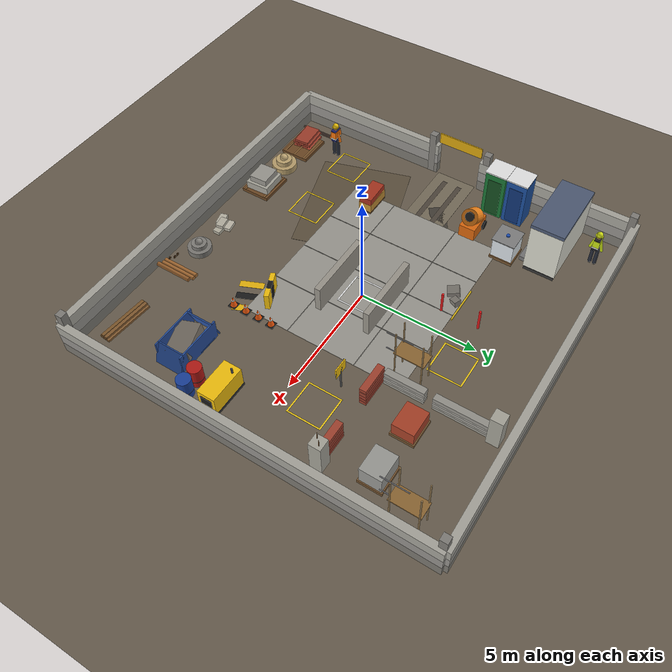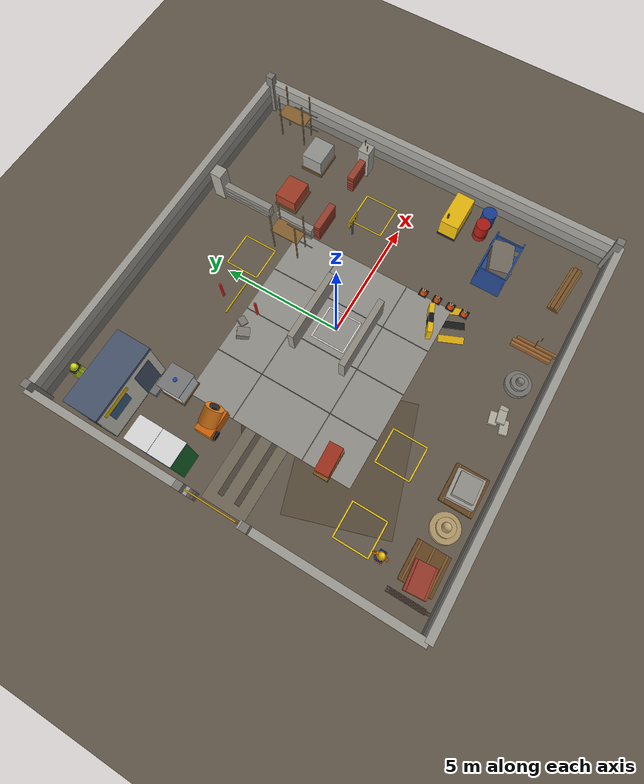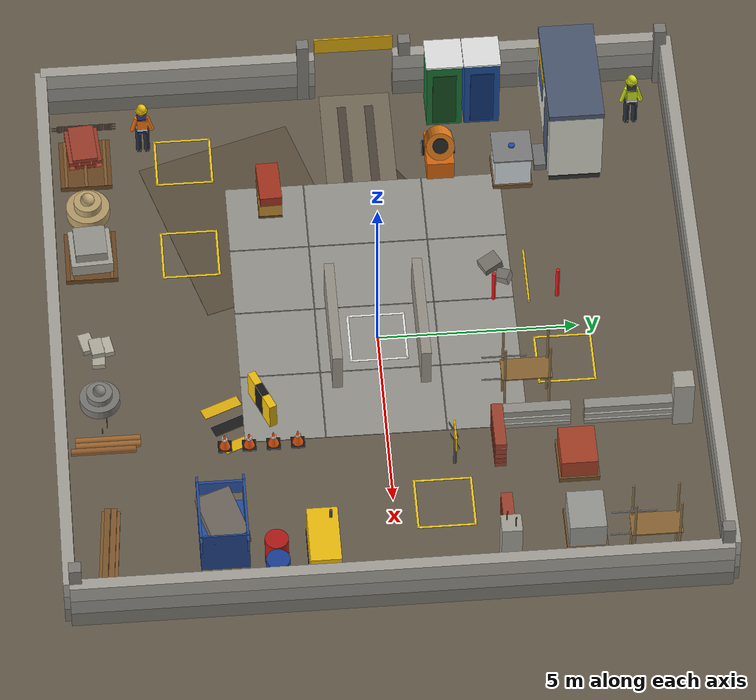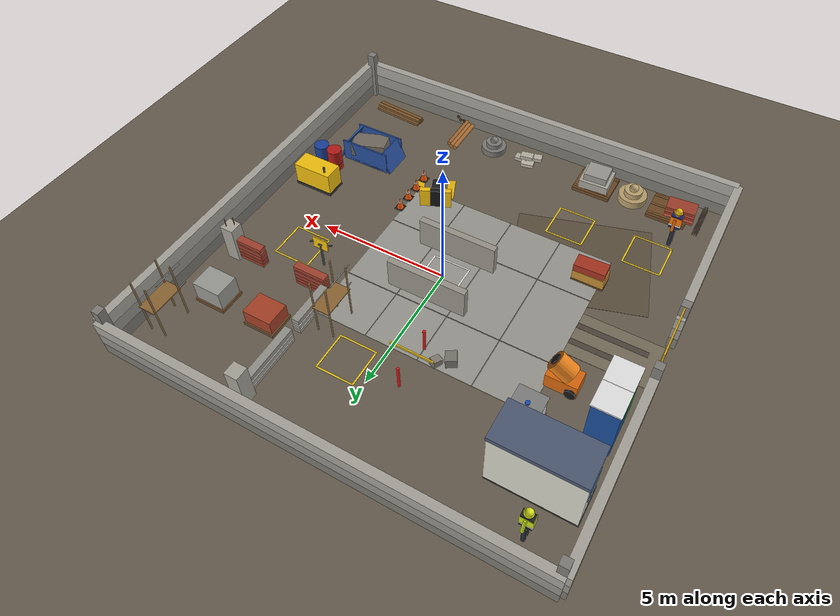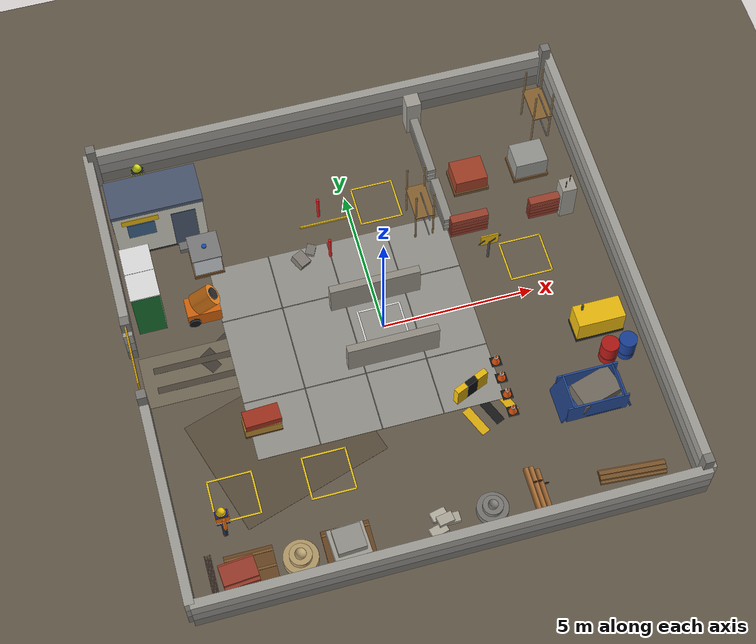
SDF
<?xml version="1.0" ?>
<sdf version="1.8">
  <world name="masonassist_world">
    <!-- Physics parameters - identical to masonassist.world, unchanged -->
    <physics type="ode">
      <max_step_size>0.001</max_step_size>
      <real_time_factor>1.0</real_time_factor>
    </physics>

    <plugin name="gz::sim::systems::Physics" filename="gz-sim-physics-system"/>
    <plugin name="gz::sim::systems::UserCommands" filename="gz-sim-user-commands-system"/>
    <plugin name="gz::sim::systems::SceneBroadcaster" filename="gz-sim-scene-broadcaster-system"/>
    <plugin name="gz::sim::systems::Contact" filename="gz-sim-contact-system"/>
    <plugin name="gz::sim::systems::Imu" filename="gz-sim-imu-system"/>
    <plugin name="gz::sim::systems::Sensors" filename="gz-sim-sensors-system">
      <render_engine>ogre2</render_engine>
    </plugin>

    <gravity>0 0 -9.8</gravity>

    <scene>
      <ambient>0.55 0.52 0.5 1</ambient>
      <background>0.62 0.68 0.75 1</background>
      <shadows>true</shadows>
      <grid>false</grid>
    </scene>

    <gui fullscreen="false">
      <plugin filename="MinimalScene" name="3D View">
        <gz-gui>
          <title>3D View</title>
          <property type="bool" key="showTitleBar">false</property>
          <property type="string" key="state">docked</property>
        </gz-gui>
        <engine>ogre2</engine>
        <scene>scene</scene>
        <ambient_light>0.55 0.52 0.5</ambient_light>
        <background_color>0.62 0.68 0.75</background_color>
        <camera_pose>-5.5 -5.5 3.6 0 0.3 0.78</camera_pose>
      </plugin>
      <plugin filename="EntityContextMenuPlugin" name="Entity context menu">
        <gz-gui>
          <property key="state" type="string">floating</property>
          <property key="width" type="double">5</property>
          <property key="height" type="double">5</property>
          <property key="showTitleBar" type="bool">false</property>
        </gz-gui>
      </plugin>
      <plugin filename="GzSceneManager" name="Scene Manager">
        <gz-gui>
          <property key="resizable" type="bool">false</property>
          <property key="width" type="double">5</property>
          <property key="height" type="double">5</property>
          <property key="state" type="string">floating</property>
          <property key="showTitleBar" type="bool">false</property>
        </gz-gui>
      </plugin>
      <plugin filename="InteractiveViewControl" name="Interactive view control">
        <gz-gui>
          <property key="resizable" type="bool">false</property>
          <property key="width" type="double">5</property>
          <property key="height" type="double">5</property>
          <property key="state" type="string">floating</property>
          <property key="showTitleBar" type="bool">false</property>
        </gz-gui>
      </plugin>
      <plugin filename="CameraTracking" name="Camera Tracking">
        <gz-gui>
          <property key="resizable" type="bool">false</property>
          <property key="width" type="double">5</property>
          <property key="height" type="double">5</property>
          <property key="state" type="string">floating</property>
          <property key="showTitleBar" type="bool">false</property>
        </gz-gui>
      </plugin>
      <plugin filename="WorldControl" name="World control">
        <gz-gui>
          <title>World control</title>
          <property type="bool" key="showTitleBar">false</property>
          <property type="bool" key="resizable">false</property>
          <property type="double" key="height">72</property>
          <property type="double" key="z">1</property>
          <property type="string" key="state">floating</property>
          <anchors target="3D View">
            <line own="left" target="left"/>
            <line own="bottom" target="bottom"/>
          </anchors>
        </gz-gui>
        <play_pause>true</play_pause>
        <step>true</step>
        <start_paused>false</start_paused>
        <use_event>true</use_event>
      </plugin>
      <plugin filename="WorldStats" name="World stats">
        <gz-gui>
          <title>World stats</title>
          <property type="bool" key="showTitleBar">false</property>
          <property type="bool" key="resizable">false</property>
          <property type="double" key="height">110</property>
          <property type="double" key="width">290</property>
          <property type="double" key="z">1</property>
          <property type="string" key="state">floating</property>
          <anchors target="3D View">
            <line own="right" target="right"/>
            <line own="bottom" target="bottom"/>
          </anchors>
        </gz-gui>
        <sim_time>true</sim_time>
        <real_time>true</real_time>
        <real_time_factor>true</real_time_factor>
        <iterations>true</iterations>
      </plugin>
    </gui>

    <!-- Ground: compacted-soil/concrete-yard tone, no grid. A second,
         slightly varied patch breaks up the uniform flat color. -->
    <model name="ground_plane">
      <static>true</static>
      <link name="link">
        <collision name="collision">
          <geometry><plane><normal>0 0 1</normal><size>100 100</size></plane></geometry>
          <surface><friction><ode><mu>1.0</mu><mu2>1.0</mu2></ode></friction></surface>
        </collision>
        <visual name="visual">
          <geometry><plane><normal>0 0 1</normal><size>100 100</size></plane></geometry>
          <material><ambient>0.4 0.36 0.3 1</ambient><diffuse>0.4 0.36 0.3 1</diffuse></material>
        </visual>
      </link>
    </model>
    <model name="soil_patch_1"><static>true</static><pose>-4 -3 0.005 0 0 0.3</pose>
      <link name="link"><visual name="visual"><geometry><box><size>5 4 0.01</size></box></geometry>
        <material><ambient>0.36 0.31 0.24 1</ambient><diffuse>0.36 0.31 0.24 1</diffuse></material></visual>
      </link></model>
    <model name="entrance_path"><static>true</static><pose>-6.2 0 0.005 0 0 0</pose>
      <link name="link"><visual name="visual"><geometry><box><size>3.4 1.8 0.01</size></box></geometry>
        <material><ambient>0.46 0.42 0.35 1</ambient><diffuse>0.46 0.42 0.35 1</diffuse></material></visual>
      </link></model>
    <model name="stain_patch_gate"><static>true</static><pose>-5.3 0.5 0.006 0 0 0.6</pose>
      <link name="link"><visual name="visual"><geometry><box><size>1.4 0.7 0.008</size></box></geometry>
        <material><ambient>0.26 0.24 0.21 1</ambient><diffuse>0.26 0.24 0.21 1</diffuse></material></visual>
      </link></model>

    <!-- Zone C work slab: poured concrete under the robot's main
         operating area -->
    <model name="concrete_slab">
      <static>true</static>
      <pose>-1 0 0.012 0 0 0</pose>
      <link name="link">
        <visual name="visual">
          <geometry><box><size>8 7 0.02</size></box></geometry>
          <material><ambient>0.6 0.59 0.56 1</ambient><diffuse>0.6 0.59 0.56 1</diffuse></material>
        </visual>
      </link>
    </model>

    <model name="slab_seams"><static>true</static><pose>-1 0 0.0225 0 0 0</pose>
      <link name="link">
        <visual name="v1"><pose>-2 0 0 0 0 0</pose><geometry><box><size>0.03 7 0.004</size></box></geometry>
          <material><ambient>0.38 0.37 0.35 1</ambient><diffuse>0.38 0.37 0.35 1</diffuse></material></visual>
        <visual name="v2"><pose>0 0 0 0 0 0</pose><geometry><box><size>0.03 7 0.004</size></box></geometry>
          <material><ambient>0.38 0.37 0.35 1</ambient><diffuse>0.38 0.37 0.35 1</diffuse></material></visual>
        <visual name="v3"><pose>2 0 0 0 0 0</pose><geometry><box><size>0.03 7 0.004</size></box></geometry>
          <material><ambient>0.38 0.37 0.35 1</ambient><diffuse>0.38 0.37 0.35 1</diffuse></material></visual>
        <visual name="h1"><pose>0 -1.5 0 0 0 0</pose><geometry><box><size>8 0.03 0.004</size></box></geometry>
          <material><ambient>0.38 0.37 0.35 1</ambient><diffuse>0.38 0.37 0.35 1</diffuse></material></visual>
        <visual name="h2"><pose>0 1.5 0 0 0 0</pose><geometry><box><size>8 0.03 0.004</size></box></geometry>
          <material><ambient>0.38 0.37 0.35 1</ambient><diffuse>0.38 0.37 0.35 1</diffuse></material></visual>
      </link>
    </model>

    <model name="wall_north"><static>true</static><pose>0 8 0.75 0 0 0</pose>
      <link name="link"><collision name="collision"><geometry><box><size>16 0.3 1.5</size></box></geometry></collision>
        <visual name="base"><pose>0 0 -0.5 0 0 0</pose><geometry><box><size>16 0.3 0.5</size></box></geometry>
          <material><ambient>0.48 0.47 0.44 1</ambient><diffuse>0.48 0.47 0.44 1</diffuse></material></visual>
        <visual name="mid"><pose>0 0 0 0 0 0</pose><geometry><box><size>16 0.3 0.5</size></box></geometry>
          <material><ambient>0.58 0.57 0.55 1</ambient><diffuse>0.58 0.57 0.55 1</diffuse></material></visual>
        <visual name="top"><pose>0 0 0.5 0 0 0</pose><geometry><box><size>16 0.3 0.5</size></box></geometry>
          <material><ambient>0.65 0.64 0.61 1</ambient><diffuse>0.65 0.64 0.61 1</diffuse></material></visual>
      </link></model>
    <model name="wall_south"><static>true</static><pose>0 -8 0.75 0 0 0</pose>
      <link name="link"><collision name="collision"><geometry><box><size>16 0.3 1.5</size></box></geometry></collision>
        <visual name="base"><pose>0 0 -0.5 0 0 0</pose><geometry><box><size>16 0.3 0.5</size></box></geometry>
          <material><ambient>0.48 0.47 0.44 1</ambient><diffuse>0.48 0.47 0.44 1</diffuse></material></visual>
        <visual name="mid"><pose>0 0 0 0 0 0</pose><geometry><box><size>16 0.3 0.5</size></box></geometry>
          <material><ambient>0.58 0.57 0.55 1</ambient><diffuse>0.58 0.57 0.55 1</diffuse></material></visual>
        <visual name="top"><pose>0 0 0.5 0 0 0</pose><geometry><box><size>16 0.3 0.5</size></box></geometry>
          <material><ambient>0.65 0.64 0.61 1</ambient><diffuse>0.65 0.64 0.61 1</diffuse></material></visual>
      </link></model>
    <model name="wall_east"><static>true</static><pose>8 0 0.75 0 0 1.5708</pose>
      <link name="link"><collision name="collision"><geometry><box><size>16 0.3 1.5</size></box></geometry></collision>
        <visual name="base"><pose>0 0 -0.5 0 0 0</pose><geometry><box><size>16 0.3 0.5</size></box></geometry>
          <material><ambient>0.48 0.47 0.44 1</ambient><diffuse>0.48 0.47 0.44 1</diffuse></material></visual>
        <visual name="mid"><pose>0 0 0 0 0 0</pose><geometry><box><size>16 0.3 0.5</size></box></geometry>
          <material><ambient>0.58 0.57 0.55 1</ambient><diffuse>0.58 0.57 0.55 1</diffuse></material></visual>
        <visual name="top"><pose>0 0 0.5 0 0 0</pose><geometry><box><size>16 0.3 0.5</size></box></geometry>
          <material><ambient>0.65 0.64 0.61 1</ambient><diffuse>0.65 0.64 0.61 1</diffuse></material></visual>
      </link></model>
    <model name="wall_west_a"><static>true</static><pose>-8 4.5 0.75 0 0 1.5708</pose>
      <link name="link"><collision name="collision"><geometry><box><size>7 0.3 1.5</size></box></geometry></collision>
        <visual name="base"><pose>0 0 -0.5 0 0 0</pose><geometry><box><size>7 0.3 0.5</size></box></geometry>
          <material><ambient>0.48 0.47 0.44 1</ambient><diffuse>0.48 0.47 0.44 1</diffuse></material></visual>
        <visual name="mid"><pose>0 0 0 0 0 0</pose><geometry><box><size>7 0.3 0.5</size></box></geometry>
          <material><ambient>0.58 0.57 0.55 1</ambient><diffuse>0.58 0.57 0.55 1</diffuse></material></visual>
        <visual name="top"><pose>0 0 0.5 0 0 0</pose><geometry><box><size>7 0.3 0.5</size></box></geometry>
          <material><ambient>0.65 0.64 0.61 1</ambient><diffuse>0.65 0.64 0.61 1</diffuse></material></visual>
      </link></model>
    <model name="wall_west_b"><static>true</static><pose>-8 -4.5 0.75 0 0 1.5708</pose>
      <link name="link"><collision name="collision"><geometry><box><size>7 0.3 1.5</size></box></geometry></collision>
        <visual name="base"><pose>0 0 -0.5 0 0 0</pose><geometry><box><size>7 0.3 0.5</size></box></geometry>
          <material><ambient>0.48 0.47 0.44 1</ambient><diffuse>0.48 0.47 0.44 1</diffuse></material></visual>
        <visual name="mid"><pose>0 0 0 0 0 0</pose><geometry><box><size>7 0.3 0.5</size></box></geometry>
          <material><ambient>0.58 0.57 0.55 1</ambient><diffuse>0.58 0.57 0.55 1</diffuse></material></visual>
        <visual name="top"><pose>0 0 0.5 0 0 0</pose><geometry><box><size>7 0.3 0.5</size></box></geometry>
          <material><ambient>0.65 0.64 0.61 1</ambient><diffuse>0.65 0.64 0.61 1</diffuse></material></visual>
      </link></model>
    <model name="column_ne"><static>true</static><pose>7.85 7.85 1.0 0 0 0</pose>
      <link name="link"><visual name="visual"><geometry><box><size>0.3 0.3 2.0</size></box></geometry>
        <material><ambient>0.5 0.49 0.47 1</ambient><diffuse>0.5 0.49 0.47 1</diffuse></material></visual>
        <collision name="collision"><geometry><box><size>0.3 0.3 2.0</size></box></geometry></collision>
      </link></model>
    <model name="column_nw"><static>true</static><pose>-7.85 7.85 1.0 0 0 0</pose>
      <link name="link"><visual name="visual"><geometry><box><size>0.3 0.3 2.0</size></box></geometry>
        <material><ambient>0.5 0.49 0.47 1</ambient><diffuse>0.5 0.49 0.47 1</diffuse></material></visual>
        <collision name="collision"><geometry><box><size>0.3 0.3 2.0</size></box></geometry></collision>
      </link></model>
    <model name="column_se"><static>true</static><pose>7.85 -7.85 1.0 0 0 0</pose>
      <link name="link"><visual name="visual"><geometry><box><size>0.3 0.3 2.0</size></box></geometry>
        <material><ambient>0.5 0.49 0.47 1</ambient><diffuse>0.5 0.49 0.47 1</diffuse></material></visual>
        <collision name="collision"><geometry><box><size>0.3 0.3 2.0</size></box></geometry></collision>
      </link></model>
    <model name="gate_post_a"><static>true</static><pose>-8 1.3 1.0 0 0 0</pose>
      <link name="link"><visual name="visual"><geometry><box><size>0.3 0.3 2.0</size></box></geometry>
        <material><ambient>0.5 0.49 0.47 1</ambient><diffuse>0.5 0.49 0.47 1</diffuse></material></visual>
        <collision name="collision"><geometry><box><size>0.3 0.3 2.0</size></box></geometry></collision>
      </link></model>
    <model name="gate_post_b"><static>true</static><pose>-8 -1.3 1.0 0 0 0</pose>
      <link name="link"><visual name="visual"><geometry><box><size>0.3 0.3 2.0</size></box></geometry>
        <material><ambient>0.5 0.49 0.47 1</ambient><diffuse>0.5 0.49 0.47 1</diffuse></material></visual>
        <collision name="collision"><geometry><box><size>0.3 0.3 2.0</size></box></geometry></collision>
      </link></model>
    <model name="gate_sign"><static>true</static><pose>-8 0 1.9 0 0 1.5708</pose>
      <link name="link"><visual name="visual"><geometry><box><size>2.0 0.05 0.5</size></box></geometry>
        <material><ambient>0.85 0.65 0.05 1</ambient><diffuse>0.85 0.65 0.05 1</diffuse></material></visual>
      </link></model>

    <model name="wall_a_left"><static>true</static><pose>3.65 2.7 0.6 0 0 0</pose>
      <link name="link">
        <collision name="collision"><geometry><box><size>1.3 0.3 1.2</size></box></geometry></collision>
        <visual name="c1"><pose>0 0 -0.42 0 0 0</pose><geometry><box><size>1.26 0.28 0.14</size></box></geometry>
          <material><ambient>0.62 0.25 0.18 1</ambient><diffuse>0.62 0.25 0.18 1</diffuse></material></visual>
        <visual name="c2"><pose>0 0 -0.25 0 0 0</pose><geometry><box><size>1.26 0.28 0.14</size></box></geometry>
          <material><ambient>0.58 0.23 0.16 1</ambient><diffuse>0.58 0.23 0.16 1</diffuse></material></visual>
        <visual name="c3"><pose>0 0 -0.08 0 0 0</pose><geometry><box><size>1.26 0.28 0.14</size></box></geometry>
          <material><ambient>0.64 0.26 0.19 1</ambient><diffuse>0.64 0.26 0.19 1</diffuse></material></visual>
        <visual name="c4"><pose>0 0 0.1 0 0 0</pose><geometry><box><size>1.26 0.28 0.18</size></box></geometry>
          <material><ambient>0.6 0.25 0.18 1</ambient><diffuse>0.6 0.25 0.18 1</diffuse></material></visual>
        <visual name="c5"><pose>0 0 0.32 0 0 0</pose><geometry><box><size>1.26 0.28 0.14</size></box></geometry>
          <material><ambient>0.63 0.26 0.18 1</ambient><diffuse>0.63 0.26 0.18 1</diffuse></material></visual>
      </link>
    </model>
    <model name="wall_a_right"><static>true</static><pose>6.35 2.7 0.6 0 0 0</pose>
      <link name="link">
        <collision name="collision"><geometry><box><size>1.3 0.3 1.2</size></box></geometry></collision>
        <visual name="c1"><pose>0 0 -0.42 0 0 0</pose><geometry><box><size>1.26 0.28 0.14</size></box></geometry>
          <material><ambient>0.62 0.25 0.18 1</ambient><diffuse>0.62 0.25 0.18 1</diffuse></material></visual>
        <visual name="c2"><pose>0 0 -0.25 0 0 0</pose><geometry><box><size>1.26 0.28 0.14</size></box></geometry>
          <material><ambient>0.58 0.23 0.16 1</ambient><diffuse>0.58 0.23 0.16 1</diffuse></material></visual>
        <visual name="c3"><pose>0 0 -0.08 0 0 0</pose><geometry><box><size>1.26 0.28 0.14</size></box></geometry>
          <material><ambient>0.64 0.26 0.19 1</ambient><diffuse>0.64 0.26 0.19 1</diffuse></material></visual>
        <visual name="c4"><pose>0 0 0.1 0 0 0</pose><geometry><box><size>1.26 0.28 0.18</size></box></geometry>
          <material><ambient>0.6 0.25 0.18 1</ambient><diffuse>0.6 0.25 0.18 1</diffuse></material></visual>
        <visual name="c5"><pose>0 0 0.32 0 0 0</pose><geometry><box><size>1.26 0.28 0.14</size></box></geometry>
          <material><ambient>0.63 0.26 0.18 1</ambient><diffuse>0.63 0.26 0.18 1</diffuse></material></visual>
      </link>
    </model>
    <model name="wall_b_lower"><static>true</static><pose>3.0 3.7 0.6 0 0 1.5708</pose>
      <link name="link">
        <collision name="collision"><geometry><box><size>1.7 0.3 1.2</size></box></geometry></collision>
        <visual name="c1"><pose>0 0 -0.42 0 0 0</pose><geometry><box><size>1.66 0.28 0.14</size></box></geometry>
          <material><ambient>0.6 0.59 0.56 1</ambient><diffuse>0.6 0.59 0.56 1</diffuse></material></visual>
        <visual name="c2"><pose>0 0 -0.2 0 0 0</pose><geometry><box><size>1.66 0.28 0.14</size></box></geometry>
          <material><ambient>0.63 0.62 0.59 1</ambient><diffuse>0.63 0.62 0.59 1</diffuse></material></visual>
        <visual name="c3"><pose>0 0 0.05 0 0 0</pose><geometry><box><size>1.66 0.28 0.2</size></box></geometry>
          <material><ambient>0.58 0.57 0.54 1</ambient><diffuse>0.58 0.57 0.54 1</diffuse></material></visual>
      </link>
    </model>
    <model name="wall_b_upper"><static>true</static><pose>3.0 6.0 0.6 0 0 1.5708</pose>
      <link name="link">
        <collision name="collision"><geometry><box><size>2.3 0.3 1.2</size></box></geometry></collision>
        <visual name="c1"><pose>0 0 -0.42 0 0 0</pose><geometry><box><size>2.26 0.28 0.14</size></box></geometry>
          <material><ambient>0.6 0.59 0.56 1</ambient><diffuse>0.6 0.59 0.56 1</diffuse></material></visual>
        <visual name="c2"><pose>0 0 -0.2 0 0 0</pose><geometry><box><size>2.26 0.28 0.14</size></box></geometry>
          <material><ambient>0.63 0.62 0.59 1</ambient><diffuse>0.63 0.62 0.59 1</diffuse></material></visual>
        <visual name="c3"><pose>0 0 0.05 0 0 0</pose><geometry><box><size>2.26 0.28 0.2</size></box></geometry>
          <material><ambient>0.58 0.57 0.54 1</ambient><diffuse>0.58 0.57 0.54 1</diffuse></material></visual>
      </link>
    </model>
    <model name="col_bld_1"><static>true</static><pose>7.0 2.7 0.75 0 0 0</pose>
      <link name="link"><visual name="visual"><geometry><box><size>0.5 0.5 1.5</size></box></geometry>
        <material><ambient>0.65 0.64 0.6 1</ambient><diffuse>0.65 0.64 0.6 1</diffuse></material></visual>
        <collision name="collision"><geometry><box><size>0.5 0.5 1.5</size></box></geometry></collision>
      </link></model>
    <model name="col_bld_2"><static>true</static><pose>3.0 7.3 0.75 0 0 0</pose>
      <link name="link"><visual name="visual"><geometry><box><size>0.5 0.5 1.5</size></box></geometry>
        <material><ambient>0.65 0.64 0.6 1</ambient><diffuse>0.65 0.64 0.6 1</diffuse></material></visual>
        <collision name="collision"><geometry><box><size>0.5 0.5 1.5</size></box></geometry></collision>
      </link></model>
    <model name="rebar_sticking_up"><static>true</static><pose>7.0 2.7 1.6 0 0 0</pose>
      <link name="link">
        <visual name="r1"><pose>0.1 0.1 0 0 0 0</pose><geometry><cylinder><radius>0.015</radius><length>0.5</length></cylinder></geometry>
          <material><ambient>0.45 0.3 0.15 1</ambient><diffuse>0.45 0.3 0.15 1</diffuse></material></visual>
        <visual name="r2"><pose>-0.1 -0.1 0 0 0 0</pose><geometry><cylinder><radius>0.015</radius><length>0.5</length></cylinder></geometry>
          <material><ambient>0.45 0.3 0.15 1</ambient><diffuse>0.45 0.3 0.15 1</diffuse></material></visual>
      </link></model>

    <!-- Lightweight scaffolding against the building's west wall - 4
         poles, 2 horizontal braces, 1 platform plank. One collision box
         covering the whole footprint. -->
    <model name="scaffold_1"><static>true</static><pose>2.2 3.5 0 0 0 0</pose>
      <link name="link">
        <collision name="collision"><pose>0 0 1.2 0 0 0</pose><geometry><box><size>0.7 1.3 2.4</size></box></geometry></collision>
        <visual name="pole1"><pose>-0.3 -0.55 1.2 0 0 0</pose><geometry><cylinder><radius>0.03</radius><length>2.4</length></cylinder></geometry>
          <material><ambient>0.55 0.45 0.3 1</ambient><diffuse>0.55 0.45 0.3 1</diffuse></material></visual>
        <visual name="pole2"><pose>0.3 -0.55 1.2 0 0 0</pose><geometry><cylinder><radius>0.03</radius><length>2.4</length></cylinder></geometry>
          <material><ambient>0.55 0.45 0.3 1</ambient><diffuse>0.55 0.45 0.3 1</diffuse></material></visual>
        <visual name="pole3"><pose>-0.3 0.55 1.2 0 0 0</pose><geometry><cylinder><radius>0.03</radius><length>2.4</length></cylinder></geometry>
          <material><ambient>0.55 0.45 0.3 1</ambient><diffuse>0.55 0.45 0.3 1</diffuse></material></visual>
        <visual name="pole4"><pose>0.3 0.55 1.2 0 0 0</pose><geometry><cylinder><radius>0.03</radius><length>2.4</length></cylinder></geometry>
          <material><ambient>0.55 0.45 0.3 1</ambient><diffuse>0.55 0.45 0.3 1</diffuse></material></visual>
        <visual name="brace_low"><pose>0 -0.55 0.9 1.5708 0 0</pose><geometry><cylinder><radius>0.02</radius><length>1.1</length></cylinder></geometry>
          <material><ambient>0.5 0.5 0.52 1</ambient><diffuse>0.5 0.5 0.52 1</diffuse></material></visual>
        <visual name="brace_high"><pose>0 -0.55 1.8 1.5708 0 0</pose><geometry><cylinder><radius>0.02</radius><length>1.1</length></cylinder></geometry>
          <material><ambient>0.5 0.5 0.52 1</ambient><diffuse>0.5 0.5 0.52 1</diffuse></material></visual>
        <visual name="platform"><pose>0 0 1.25 0 0 0</pose><geometry><box><size>0.65 1.25 0.04</size></box></geometry>
          <material><ambient>0.55 0.4 0.2 1</ambient><diffuse>0.55 0.4 0.2 1</diffuse></material></visual>
      </link></model>

    <!-- Hazard warning sign on a post, facing the open work area -->
    <model name="warning_sign"><static>true</static><pose>4.0 1.6 0 0 0 -1.5708</pose>
      <link name="link">
        <!-- collision matches the visuals: a 4 cm post and the board above
             robot height (the registry box in worker_mover.py stays larger,
             so the planner still keeps its distance) -->
        <collision name="post_collision"><pose>0 0 0.5 0 0 0</pose><geometry><cylinder><radius>0.04</radius><length>1.0</length></cylinder></geometry></collision>
        <collision name="board_collision"><pose>0 0 1.1 0 0 0</pose><geometry><box><size>0.04 0.6 0.5</size></box></geometry></collision>
        <visual name="post"><pose>0 0 0.5 0 0 0</pose><geometry><cylinder><radius>0.04</radius><length>1.0</length></cylinder></geometry>
          <material><ambient>0.3 0.3 0.3 1</ambient><diffuse>0.3 0.3 0.3 1</diffuse></material></visual>
        <visual name="board"><pose>0 0 1.1 0 0 0</pose><geometry><box><size>0.04 0.6 0.5</size></box></geometry>
          <material><ambient>0.95 0.75 0.05 1</ambient><diffuse>0.95 0.75 0.05 1</diffuse></material></visual>
        <visual name="board_stripe1"><pose>0.025 -0.18 1.1 0 0 0.4</pose><geometry><box><size>0.01 0.5 0.08</size></box></geometry>
          <material><ambient>0.1 0.1 0.1 1</ambient><diffuse>0.1 0.1 0.1 1</diffuse></material></visual>
        <visual name="board_stripe2"><pose>0.025 0.18 1.1 0 0 0.4</pose><geometry><box><size>0.01 0.5 0.08</size></box></geometry>
          <material><ambient>0.1 0.1 0.1 1</ambient><diffuse>0.1 0.1 0.1 1</diffuse></material></visual>
      </link></model>

    <model name="pallet_bricks"><static>true</static><pose>-6 -7 0.1 0 0 0</pose>
      <link name="link">
        <collision name="collision"><geometry><box><size>1.5 1.3 0.15</size></box></geometry></collision>
        <visual name="visual"><geometry><box><size>1.5 1.3 0.15</size></box></geometry>
          <material><ambient>0.42 0.28 0.14 1</ambient><diffuse>0.42 0.28 0.14 1</diffuse></material></visual>
        <visual name="slat1"><pose>0 -0.5 0.08 0 0 0</pose><geometry><box><size>1.5 0.08 0.03</size></box></geometry>
          <material><ambient>0.5 0.35 0.18 1</ambient><diffuse>0.5 0.35 0.18 1</diffuse></material></visual>
        <visual name="slat2"><pose>0 0 0.08 0 0 0</pose><geometry><box><size>1.5 0.08 0.03</size></box></geometry>
          <material><ambient>0.5 0.35 0.18 1</ambient><diffuse>0.5 0.35 0.18 1</diffuse></material></visual>
        <visual name="slat3"><pose>0 0.5 0.08 0 0 0</pose><geometry><box><size>1.5 0.08 0.03</size></box></geometry>
          <material><ambient>0.5 0.35 0.18 1</ambient><diffuse>0.5 0.35 0.18 1</diffuse></material></visual>
      </link>
    </model>
    <model name="brick_stack_1"><static>true</static><pose>-6 -7 0.3 0 0 0.08</pose>
      <link name="link">
        <collision name="collision"><geometry><box><size>1.2 1.0 0.5</size></box></geometry></collision>
        <visual name="v_row1a"><pose>-0.4 -0.3 -0.17 0 0 0</pose><geometry><box><size>1.1 0.24 0.1</size></box></geometry>
          <material><ambient>0.62 0.24 0.17 1</ambient><diffuse>0.62 0.24 0.17 1</diffuse></material></visual>
        <visual name="v_row1b"><pose>-0.4 0.0 -0.17 0 0 0</pose><geometry><box><size>1.1 0.24 0.1</size></box></geometry>
          <material><ambient>0.58 0.22 0.15 1</ambient><diffuse>0.58 0.22 0.15 1</diffuse></material></visual>
        <visual name="v_row1c"><pose>-0.4 0.3 -0.17 0 0 0</pose><geometry><box><size>1.1 0.24 0.1</size></box></geometry>
          <material><ambient>0.65 0.26 0.18 1</ambient><diffuse>0.65 0.26 0.18 1</diffuse></material></visual>
        <visual name="v_row2a"><pose>-0.4 -0.15 -0.05 0 0 0</pose><geometry><box><size>1.1 0.24 0.1</size></box></geometry>
          <material><ambient>0.6 0.23 0.16 1</ambient><diffuse>0.6 0.23 0.16 1</diffuse></material></visual>
        <visual name="v_row2b"><pose>-0.4 0.15 -0.05 0 0 0</pose><geometry><box><size>1.1 0.24 0.1</size></box></geometry>
          <material><ambient>0.63 0.25 0.17 1</ambient><diffuse>0.63 0.25 0.17 1</diffuse></material></visual>
        <visual name="v_row3a"><pose>-0.4 -0.3 0.07 0 0 0</pose><geometry><box><size>1.1 0.24 0.1</size></box></geometry>
          <material><ambient>0.61 0.24 0.16 1</ambient><diffuse>0.61 0.24 0.16 1</diffuse></material></visual>
        <visual name="v_row3b"><pose>-0.4 0.0 0.07 0 0 0</pose><geometry><box><size>1.1 0.24 0.1</size></box></geometry>
          <material><ambient>0.64 0.25 0.17 1</ambient><diffuse>0.64 0.25 0.17 1</diffuse></material></visual>
        <visual name="v_row3c"><pose>-0.4 0.3 0.07 0 0 0</pose><geometry><box><size>1.1 0.24 0.1</size></box></geometry>
          <material><ambient>0.6 0.23 0.16 1</ambient><diffuse>0.6 0.23 0.16 1</diffuse></material></visual>
        <visual name="v_row4"><pose>-0.4 0.0 0.19 0 0 0</pose><geometry><box><size>1.1 0.64 0.1</size></box></geometry>
          <material><ambient>0.62 0.24 0.17 1</ambient><diffuse>0.62 0.24 0.17 1</diffuse></material></visual>
      </link>
    </model>

    <model name="pallet_blocks"><static>true</static><pose>-3 -7 0.1 0 0 0</pose>
      <link name="link">
        <collision name="collision"><geometry><box><size>1.5 1.3 0.15</size></box></geometry></collision>
        <visual name="visual"><geometry><box><size>1.5 1.3 0.15</size></box></geometry>
          <material><ambient>0.42 0.28 0.14 1</ambient><diffuse>0.42 0.28 0.14 1</diffuse></material></visual>
        <visual name="slat1"><pose>0 -0.5 0.08 0 0 0</pose><geometry><box><size>1.5 0.08 0.03</size></box></geometry>
          <material><ambient>0.5 0.35 0.18 1</ambient><diffuse>0.5 0.35 0.18 1</diffuse></material></visual>
        <visual name="slat2"><pose>0 0.5 0.08 0 0 0</pose><geometry><box><size>1.5 0.08 0.03</size></box></geometry>
          <material><ambient>0.5 0.35 0.18 1</ambient><diffuse>0.5 0.35 0.18 1</diffuse></material></visual>
      </link>
    </model>
    <model name="block_stack_2"><static>true</static><pose>-3 -7 0.52 0 0 0.05</pose>
      <link name="link">
        <collision name="collision"><geometry><box><size>1.2 1.1 0.7</size></box></geometry></collision>
        <visual name="v_a"><pose>0 0 -0.17 0 0 0</pose><geometry><box><size>1.15 1.05 0.35</size></box></geometry>
          <material><ambient>0.65 0.64 0.6 1</ambient><diffuse>0.65 0.64 0.6 1</diffuse></material></visual>
        <visual name="v_b"><pose>0 0 0.15 0 0 0</pose><geometry><box><size>0.9 0.8 0.28</size></box></geometry>
          <material><ambient>0.6 0.59 0.56 1</ambient><diffuse>0.6 0.59 0.56 1</diffuse></material></visual>
      </link>
    </model>

    <model name="cement_bags"><static>true</static><pose>0 -7 0.2 0 0 0.15</pose>
      <link name="link">
        <collision name="collision"><geometry><box><size>1.3 1.1 0.4</size></box></geometry></collision>
        <visual name="v1"><pose>-0.3 -0.2 -0.08 0 0 0.1</pose><geometry><box><size>0.55 0.32 0.15</size></box></geometry>
          <material><ambient>0.72 0.7 0.64 1</ambient><diffuse>0.72 0.7 0.64 1</diffuse></material></visual>
        <visual name="v2"><pose>0.2 0.0 -0.08 0 0 -0.15</pose><geometry><box><size>0.55 0.32 0.15</size></box></geometry>
          <material><ambient>0.7 0.68 0.62 1</ambient><diffuse>0.7 0.68 0.62 1</diffuse></material></visual>
        <visual name="v3"><pose>-0.1 0.25 -0.08 0 0 0.05</pose><geometry><box><size>0.5 0.32 0.15</size></box></geometry>
          <material><ambient>0.74 0.72 0.66 1</ambient><diffuse>0.74 0.72 0.66 1</diffuse></material></visual>
        <visual name="v4"><pose>0.0 0.0 0.08 0 0 0.02</pose><geometry><box><size>0.5 0.32 0.15</size></box></geometry>
          <material><ambient>0.71 0.69 0.63 1</ambient><diffuse>0.71 0.69 0.63 1</diffuse></material></visual>
      </link>
    </model>

    <model name="pipe_pile"><static>true</static><pose>3 -7 0.25 1.5708 0 0</pose>
      <link name="link">
        <collision name="collision"><geometry><box><size>0.6 1.8 0.6</size></box></geometry></collision>
        <visual name="p1"><pose>-0.16 0 -0.14 0 0 0</pose><geometry><cylinder><radius>0.09</radius><length>1.6</length></cylinder></geometry>
          <material><ambient>0.65 0.42 0.2 1</ambient><diffuse>0.65 0.42 0.2 1</diffuse></material></visual>
        <visual name="p1cap"><pose>-0.16 0.81 -0.14 0 0 0</pose><geometry><cylinder><radius>0.065</radius><length>0.02</length></cylinder></geometry>
          <material><ambient>0.3 0.2 0.1 1</ambient><diffuse>0.3 0.2 0.1 1</diffuse></material></visual>
        <visual name="p2"><pose>0.0 0 -0.14 0 0 0</pose><geometry><cylinder><radius>0.09</radius><length>1.6</length></cylinder></geometry>
          <material><ambient>0.65 0.42 0.2 1</ambient><diffuse>0.65 0.42 0.2 1</diffuse></material></visual>
        <visual name="p2cap"><pose>0.0 0.81 -0.14 0 0 0</pose><geometry><cylinder><radius>0.065</radius><length>0.02</length></cylinder></geometry>
          <material><ambient>0.3 0.2 0.1 1</ambient><diffuse>0.3 0.2 0.1 1</diffuse></material></visual>
        <visual name="p3"><pose>0.16 0 -0.02 0 0 0</pose><geometry><cylinder><radius>0.09</radius><length>1.6</length></cylinder></geometry>
          <material><ambient>0.6 0.38 0.18 1</ambient><diffuse>0.6 0.38 0.18 1</diffuse></material></visual>
        <visual name="p3cap"><pose>0.16 0.81 -0.02 0 0 0</pose><geometry><cylinder><radius>0.065</radius><length>0.02</length></cylinder></geometry>
          <material><ambient>0.3 0.2 0.1 1</ambient><diffuse>0.3 0.2 0.1 1</diffuse></material></visual>
      </link>
    </model>

    <model name="timber_stack"><static>true</static><pose>6 -7 0.2 0 0 -0.08</pose>
      <link name="link">
        <collision name="collision"><geometry><box><size>2.2 0.5 0.4</size></box></geometry></collision>
        <visual name="t1"><pose>0 -0.14 -0.08 0 0 0</pose><geometry><box><size>2.1 0.14 0.1</size></box></geometry>
          <material><ambient>0.5 0.35 0.18 1</ambient><diffuse>0.5 0.35 0.18 1</diffuse></material></visual>
        <visual name="t2"><pose>0 0.02 -0.08 0 0 0</pose><geometry><box><size>2.1 0.14 0.1</size></box></geometry>
          <material><ambient>0.47 0.32 0.16 1</ambient><diffuse>0.47 0.32 0.16 1</diffuse></material></visual>
        <visual name="t3"><pose>0 0.18 -0.08 0 0 0</pose><geometry><box><size>2.1 0.14 0.1</size></box></geometry>
          <material><ambient>0.52 0.36 0.19 1</ambient><diffuse>0.52 0.36 0.19 1</diffuse></material></visual>
        <visual name="t4"><pose>0 -0.06 0.04 0 0 0</pose><geometry><box><size>2.1 0.14 0.1</size></box></geometry>
          <material><ambient>0.49 0.34 0.17 1</ambient><diffuse>0.49 0.34 0.17 1</diffuse></material></visual>
        <visual name="t5"><pose>0 0.1 0.04 0 0 0</pose><geometry><box><size>2.1 0.14 0.1</size></box></geometry>
          <material><ambient>0.51 0.35 0.18 1</ambient><diffuse>0.51 0.35 0.18 1</diffuse></material></visual>
      </link>
    </model>

    <model name="rebar_bundle"><static>true</static><pose>-7.2 -7 0.15 1.5708 0 0</pose>
      <link name="link">
        <collision name="collision"><geometry><box><size>0.4 1.6 0.3</size></box></geometry></collision>
        <visual name="r1"><pose>-0.08 0 -0.08 0 0 0</pose><geometry><cylinder><radius>0.018</radius><length>1.5</length></cylinder></geometry>
          <material><ambient>0.4 0.32 0.28 1</ambient><diffuse>0.4 0.32 0.28 1</diffuse></material></visual>
        <visual name="r2"><pose>0.0 0 -0.08 0 0 0</pose><geometry><cylinder><radius>0.018</radius><length>1.5</length></cylinder></geometry>
          <material><ambient>0.42 0.34 0.3 1</ambient><diffuse>0.42 0.34 0.3 1</diffuse></material></visual>
        <visual name="r3"><pose>0.08 0 -0.08 0 0 0</pose><geometry><cylinder><radius>0.018</radius><length>1.5</length></cylinder></geometry>
          <material><ambient>0.4 0.32 0.28 1</ambient><diffuse>0.4 0.32 0.28 1</diffuse></material></visual>
        <visual name="r4"><pose>-0.04 0 0.05 0 0 0</pose><geometry><cylinder><radius>0.018</radius><length>1.5</length></cylinder></geometry>
          <material><ambient>0.41 0.33 0.29 1</ambient><diffuse>0.41 0.33 0.29 1</diffuse></material></visual>
        <visual name="r5"><pose>0.04 0 0.05 0 0 0</pose><geometry><cylinder><radius>0.018</radius><length>1.5</length></cylinder></geometry>
          <material><ambient>0.4 0.32 0.28 1</ambient><diffuse>0.4 0.32 0.28 1</diffuse></material></visual>
      </link>
    </model>

    <!-- Sand pile and aggregate pile: tapered stacked-cylinder mounds
         (no reliable cone primitive), filling the open gaps between the
         other Zone B storage items. -->
    <model name="sand_pile"><static>true</static><pose>-4.5 -7 0 0 0 0.2</pose>
      <link name="link">
        <collision name="collision"><geometry><box><size>1.2 1.2 0.7</size></box></geometry></collision>
        <visual name="base"><pose>0 0 0.15 0 0 0</pose><geometry><cylinder><radius>0.55</radius><length>0.3</length></cylinder></geometry>
          <material><ambient>0.72 0.62 0.42 1</ambient><diffuse>0.72 0.62 0.42 1</diffuse></material></visual>
        <visual name="mid"><pose>0 0 0.38 0 0 0</pose><geometry><cylinder><radius>0.35</radius><length>0.28</length></cylinder></geometry>
          <material><ambient>0.74 0.64 0.44 1</ambient><diffuse>0.74 0.64 0.44 1</diffuse></material></visual>
        <visual name="top"><pose>0 0 0.56 0 0 0</pose><geometry><sphere><radius>0.18</radius></sphere></geometry>
          <material><ambient>0.76 0.66 0.46 1</ambient><diffuse>0.76 0.66 0.46 1</diffuse></material></visual>
      </link>
    </model>
    <model name="aggregate_pile"><static>true</static><pose>1.5 -7 0 0 0 -0.15</pose>
      <link name="link">
        <collision name="collision"><geometry><box><size>1.1 1.1 0.6</size></box></geometry></collision>
        <visual name="base"><pose>0 0 0.13 0 0 0</pose><geometry><cylinder><radius>0.5</radius><length>0.26</length></cylinder></geometry>
          <material><ambient>0.48 0.47 0.45 1</ambient><diffuse>0.48 0.47 0.45 1</diffuse></material></visual>
        <visual name="mid"><pose>0 0 0.33 0 0 0</pose><geometry><cylinder><radius>0.32</radius><length>0.24</length></cylinder></geometry>
          <material><ambient>0.5 0.49 0.47 1</ambient><diffuse>0.5 0.49 0.47 1</diffuse></material></visual>
        <visual name="top"><pose>0 0 0.48 0 0 0</pose><geometry><sphere><radius>0.16</radius></sphere></geometry>
          <material><ambient>0.52 0.51 0.49 1</ambient><diffuse>0.52 0.51 0.49 1</diffuse></material></visual>
      </link>
    </model>

    <model name="partition_a"><static>true</static><pose>0 1.1 0.6 0 0 0</pose>
      <link name="link"><collision name="collision"><geometry><box><size>3 0.25 1.2</size></box></geometry></collision>
        <visual name="visual"><geometry><box><size>3 0.25 1.2</size></box></geometry>
          <material><ambient>0.6 0.58 0.54 1</ambient><diffuse>0.6 0.58 0.54 1</diffuse></material></visual>
      </link></model>
    <model name="partition_b"><static>true</static><pose>0 -1.1 0.6 0 0 0</pose>
      <link name="link"><collision name="collision"><geometry><box><size>3 0.25 1.2</size></box></geometry></collision>
        <visual name="visual"><geometry><box><size>3 0.25 1.2</size></box></geometry>
          <material><ambient>0.6 0.58 0.54 1</ambient><diffuse>0.6 0.58 0.54 1</diffuse></material></visual>
      </link></model>

    <model name="barrier_1"><static>true</static><pose>2 -3 0.4 0 0 0.4</pose>
      <link name="link">
        <collision name="collision"><geometry><box><size>1.2 0.2 0.8</size></box></geometry></collision>
        <visual name="s1"><pose>-0.4 0 0 0 0 0</pose><geometry><box><size>0.4 0.2 0.8</size></box></geometry>
          <material><ambient>0.95 0.75 0.05 1</ambient><diffuse>0.95 0.75 0.05 1</diffuse></material></visual>
        <visual name="s2"><pose>0 0 0 0 0 0</pose><geometry><box><size>0.4 0.2 0.8</size></box></geometry>
          <material><ambient>0.08 0.08 0.08 1</ambient><diffuse>0.08 0.08 0.08 1</diffuse></material></visual>
        <visual name="s3"><pose>0.4 0 0 0 0 0</pose><geometry><box><size>0.4 0.2 0.8</size></box></geometry>
          <material><ambient>0.95 0.75 0.05 1</ambient><diffuse>0.95 0.75 0.05 1</diffuse></material></visual>
      </link>
    </model>
    <model name="work_zone_marking"><static>true</static><pose>2 -3 0.015 0 0 0.4</pose>
      <link name="link">
        <visual name="h1"><pose>-0.5 -0.9 0 0 0 0</pose><geometry><box><size>0.3 1.0 0.01</size></box></geometry>
          <material><ambient>0.9 0.7 0.05 1</ambient><diffuse>0.9 0.7 0.05 1</diffuse></material></visual>
        <visual name="h2"><pose>0.1 -0.9 0 0 0 0</pose><geometry><box><size>0.3 1.0 0.01</size></box></geometry>
          <material><ambient>0.1 0.1 0.1 1</ambient><diffuse>0.1 0.1 0.1 1</diffuse></material></visual>
        <visual name="h3"><pose>0.7 -0.9 0 0 0 0</pose><geometry><box><size>0.3 1.0 0.01</size></box></geometry>
          <material><ambient>0.9 0.7 0.05 1</ambient><diffuse>0.9 0.7 0.05 1</diffuse></material></visual>
      </link>
    </model>

    <!-- Safety-tape zone, relocated off both worker lanes (verified) -->
    <model name="safety_post_a"><static>true</static><pose>-1 3 0.5 0 0 0</pose>
      <link name="link"><visual name="visual"><geometry><cylinder><radius>0.05</radius><length>1.0</length></cylinder></geometry>
        <material><ambient>0.9 0.1 0.1 1</ambient><diffuse>0.9 0.1 0.1 1</diffuse></material></visual>
        <collision name="collision"><geometry><cylinder><radius>0.05</radius><length>1.0</length></cylinder></geometry></collision>
      </link></model>
    <model name="safety_post_b"><static>true</static><pose>-1 4.6 0.5 0 0 0</pose>
      <link name="link"><visual name="visual"><geometry><cylinder><radius>0.05</radius><length>1.0</length></cylinder></geometry>
        <material><ambient>0.9 0.1 0.1 1</ambient><diffuse>0.9 0.1 0.1 1</diffuse></material></visual>
        <collision name="collision"><geometry><cylinder><radius>0.05</radius><length>1.0</length></cylinder></geometry></collision>
      </link></model>
    <model name="safety_tape"><static>true</static><pose>-1 3.8 0.85 0 0 0</pose>
      <link name="link"><visual name="visual"><geometry><box><size>1.6 0.05 0.08</size></box></geometry>
        <material><ambient>0.9 0.75 0.1 1</ambient><diffuse>0.9 0.75 0.1 1</diffuse></material></visual>
      </link></model>

    <model name="rubble_1"><static>true</static><pose>-2 3 0.15 0.2 0.1 0.5</pose>
      <link name="link"><collision name="collision"><geometry><box><size>0.4 0.5 0.3</size></box></geometry></collision>
        <visual name="visual"><geometry><box><size>0.4 0.5 0.3</size></box></geometry>
          <material><ambient>0.5 0.48 0.45 1</ambient><diffuse>0.5 0.48 0.45 1</diffuse></material></visual>
      </link></model>
    <model name="rubble_2"><static>true</static><pose>-1.6 3.3 0.12 0.1 -0.2 1.1</pose>
      <link name="link"><collision name="collision"><geometry><box><size>0.35 0.3 0.25</size></box></geometry></collision>
        <visual name="visual"><geometry><box><size>0.35 0.3 0.25</size></box></geometry>
          <material><ambient>0.5 0.48 0.45 1</ambient><diffuse>0.5 0.48 0.45 1</diffuse></material></visual>
      </link></model>

    <!-- Site office: portable cabin in the north-west corner -->
    <model name="site_office"><static>true</static><pose>-6.2 5.4 0 0 0 0</pose>
      <link name="link">
        <collision name="collision"><pose>0 0 1.25 0 0 0</pose><geometry><box><size>3.0 1.4 2.5</size></box></geometry></collision>
        <collision name="steps_col"><pose>0.8 -0.85 0.1 0 0 0</pose><geometry><box><size>0.7 0.3 0.2</size></box></geometry></collision>
        <visual name="skid"><pose>0 0 0.075 0 0 0</pose><geometry><box><size>3.0 1.3 0.15</size></box></geometry>
          <material><ambient>0.2 0.2 0.2 1</ambient><diffuse>0.2 0.2 0.2 1</diffuse></material></visual>
        <visual name="body"><pose>0 0 1.25 0 0 0</pose><geometry><box><size>2.96 1.36 2.2</size></box></geometry>
          <material><ambient>0.85 0.85 0.8 1</ambient><diffuse>0.85 0.85 0.8 1</diffuse></material></visual>
        <visual name="roof"><pose>0 0 2.42 0 0 0</pose><geometry><box><size>3.0 1.4 0.16</size></box></geometry>
          <material><ambient>0.3 0.35 0.45 1</ambient><diffuse>0.3 0.35 0.45 1</diffuse></material></visual>
        <visual name="door"><pose>0.8 -0.69 1.05 0 0 0</pose><geometry><box><size>0.8 0.02 1.9</size></box></geometry>
          <material><ambient>0.3 0.35 0.45 1</ambient><diffuse>0.3 0.35 0.45 1</diffuse></material></visual>
        <visual name="window_1"><pose>-0.6 -0.69 1.5 0 0 0</pose><geometry><box><size>0.9 0.02 0.7</size></box></geometry>
          <material><ambient>0.25 0.4 0.55 1</ambient><diffuse>0.25 0.4 0.55 1</diffuse><specular>0.6 0.6 0.6 1</specular></material></visual>
        <visual name="window_2"><pose>-1.49 0 1.5 0 0 0</pose><geometry><box><size>0.02 0.8 0.7</size></box></geometry>
          <material><ambient>0.25 0.4 0.55 1</ambient><diffuse>0.25 0.4 0.55 1</diffuse><specular>0.6 0.6 0.6 1</specular></material></visual>
        <visual name="sign"><pose>-0.6 -0.70 2.05 0 0 0</pose><geometry><box><size>1.2 0.02 0.25</size></box></geometry>
          <material><ambient>0.95 0.75 0.05 1</ambient><diffuse>0.95 0.75 0.05 1</diffuse></material></visual>
        <visual name="steps"><pose>0.8 -0.85 0.1 0 0 0</pose><geometry><box><size>0.7 0.3 0.2</size></box></geometry>
          <material><ambient>0.45 0.45 0.45 1</ambient><diffuse>0.45 0.45 0.45 1</diffuse></material></visual>
      </link></model>

    <!-- Two portable toilets against the west wall -->
    <model name="portable_toilets"><static>true</static><pose>-7.2 2.72 0 0 0 0</pose>
      <link name="link">
        <collision name="collision"><pose>0 0 1.1 0 0 0</pose><geometry><box><size>0.9 1.9 2.2</size></box></geometry></collision>
        <visual name="unit_1"><pose>0 -0.48 1.1 0 0 0</pose><geometry><box><size>0.9 0.9 2.2</size></box></geometry>
          <material><ambient>0.1 0.45 0.2 1</ambient><diffuse>0.1 0.45 0.2 1</diffuse></material></visual>
        <visual name="unit_2"><pose>0 0.48 1.1 0 0 0</pose><geometry><box><size>0.9 0.9 2.2</size></box></geometry>
          <material><ambient>0.1 0.3 0.6 1</ambient><diffuse>0.1 0.3 0.6 1</diffuse></material></visual>
        <visual name="roof_1"><pose>0 -0.48 2.23 0 0 0</pose><geometry><box><size>0.95 0.95 0.06</size></box></geometry>
          <material><ambient>0.9 0.9 0.9 1</ambient><diffuse>0.9 0.9 0.9 1</diffuse></material></visual>
        <visual name="roof_2"><pose>0 0.48 2.23 0 0 0</pose><geometry><box><size>0.95 0.95 0.06</size></box></geometry>
          <material><ambient>0.9 0.9 0.9 1</ambient><diffuse>0.9 0.9 0.9 1</diffuse></material></visual>
        <visual name="door_1"><pose>0.46 -0.48 1.0 0 0 0</pose><geometry><box><size>0.02 0.6 1.8</size></box></geometry>
          <material><ambient>0.08 0.3 0.12 1</ambient><diffuse>0.08 0.3 0.12 1</diffuse></material></visual>
        <visual name="door_2"><pose>0.46 0.48 1.0 0 0 0</pose><geometry><box><size>0.02 0.6 1.8</size></box></geometry>
          <material><ambient>0.06 0.2 0.45 1</ambient><diffuse>0.06 0.2 0.45 1</diffuse></material></visual>
      </link></model>

    <!-- Concrete mixer: tilted drum on a steel frame -->
    <model name="concrete_mixer"><static>true</static><pose>-5.5 2.0 0 0 0 0</pose>
      <link name="link">
        <collision name="collision"><pose>0 0 0.65 0 0 0</pose><geometry><box><size>1.2 0.8 1.3</size></box></geometry></collision>
        <visual name="frame"><pose>0 0 0.3 0 0 0</pose><geometry><box><size>1.1 0.7 0.6</size></box></geometry>
          <material><ambient>0.85 0.4 0.05 1</ambient><diffuse>0.85 0.4 0.05 1</diffuse></material></visual>
        <visual name="drum"><pose>0.1 0 0.9 0 1.0 0</pose><geometry><cylinder><radius>0.36</radius><length>0.7</length></cylinder></geometry>
          <material><ambient>0.9 0.5 0.1 1</ambient><diffuse>0.9 0.5 0.1 1</diffuse></material></visual>
        <visual name="drum_mouth"><pose>0.38 0 1.12 0 1.0 0</pose><geometry><cylinder><radius>0.2</radius><length>0.1</length></cylinder></geometry>
          <material><ambient>0.15 0.15 0.15 1</ambient><diffuse>0.15 0.15 0.15 1</diffuse></material></visual>
        <visual name="wheel_l"><pose>-0.35 0.38 0.2 1.5708 0 0</pose><geometry><cylinder><radius>0.2</radius><length>0.08</length></cylinder></geometry>
          <material><ambient>0.08 0.08 0.08 1</ambient><diffuse>0.08 0.08 0.08 1</diffuse></material></visual>
        <visual name="wheel_r"><pose>-0.35 -0.38 0.2 1.5708 0 0</pose><geometry><cylinder><radius>0.2</radius><length>0.08</length></cylinder></geometry>
          <material><ambient>0.08 0.08 0.08 1</ambient><diffuse>0.08 0.08 0.08 1</diffuse></material></visual>
      </link></model>

    <!-- Water tank: IBC tote in a steel cage on a pallet -->
    <model name="water_tank"><static>true</static><pose>-5.0 3.8 0 0 0 0</pose>
      <link name="link">
        <collision name="collision"><pose>0 0 0.55 0 0 0</pose><geometry><box><size>1.0 1.0 1.1</size></box></geometry></collision>
        <visual name="pallet"><pose>0 0 0.07 0 0 0</pose><geometry><box><size>1.0 1.0 0.14</size></box></geometry>
          <material><ambient>0.45 0.32 0.18 1</ambient><diffuse>0.45 0.32 0.18 1</diffuse></material></visual>
        <visual name="tank"><pose>0 0 0.6 0 0 0</pose><geometry><box><size>0.92 0.92 0.9</size></box></geometry>
          <material><ambient>0.85 0.88 0.9 1</ambient><diffuse>0.85 0.88 0.9 1</diffuse></material></visual>
        <visual name="cage_top"><pose>0 0 1.07 0 0 0</pose><geometry><box><size>1.0 1.0 0.04</size></box></geometry>
          <material><ambient>0.5 0.5 0.5 1</ambient><diffuse>0.5 0.5 0.5 1</diffuse></material></visual>
        <visual name="cap"><pose>0 0 1.11 0 0 0</pose><geometry><cylinder><radius>0.08</radius><length>0.05</length></cylinder></geometry>
          <material><ambient>0.1 0.3 0.7 1</ambient><diffuse>0.1 0.3 0.7 1</diffuse></material></visual>
      </link></model>

    <!-- Formwork panel stack: deliberately close to the straight-line
         dock -> brick_pickup route, so the planner and VFH+ have to
         route around it -->
    <model name="formwork_stack"><static>true</static><pose>-4.6 -2.4 0 0 0 0</pose>
      <link name="link">
        <collision name="collision"><pose>0 0 0.4 0 0 0</pose><geometry><box><size>1.2 0.6 0.8</size></box></geometry></collision>
        <visual name="bearers"><pose>0 0 0.05 0 0 0</pose><geometry><box><size>1.2 0.6 0.1</size></box></geometry>
          <material><ambient>0.4 0.28 0.15 1</ambient><diffuse>0.4 0.28 0.15 1</diffuse></material></visual>
        <visual name="panels_low"><pose>0 0 0.3 0 0 0</pose><geometry><box><size>1.18 0.58 0.4</size></box></geometry>
          <material><ambient>0.75 0.55 0.2 1</ambient><diffuse>0.75 0.55 0.2 1</diffuse></material></visual>
        <visual name="panels_high"><pose>0.02 0 0.65 0 0 0.04</pose><geometry><box><size>1.15 0.56 0.3</size></box></geometry>
          <material><ambient>0.65 0.2 0.12 1</ambient><diffuse>0.65 0.2 0.12 1</diffuse></material></visual>
      </link></model>

    <!-- Generator and fuel drums in the east yard -->
    <model name="generator"><static>true</static><pose>6.6 -1.8 0 0 0 0</pose>
      <link name="link">
        <collision name="collision"><pose>0 0 0.5 0 0 0</pose><geometry><box><size>1.6 0.8 1.0</size></box></geometry></collision>
        <visual name="base"><pose>0 0 0.06 0 0 0</pose><geometry><box><size>1.6 0.8 0.12</size></box></geometry>
          <material><ambient>0.2 0.2 0.2 1</ambient><diffuse>0.2 0.2 0.2 1</diffuse></material></visual>
        <visual name="housing"><pose>0 0 0.55 0 0 0</pose><geometry><box><size>1.56 0.76 0.86</size></box></geometry>
          <material><ambient>0.95 0.75 0.05 1</ambient><diffuse>0.95 0.75 0.05 1</diffuse></material></visual>
        <visual name="vent"><pose>0.79 0 0.6 0 0 0</pose><geometry><box><size>0.02 0.5 0.4</size></box></geometry>
          <material><ambient>0.1 0.1 0.1 1</ambient><diffuse>0.1 0.1 0.1 1</diffuse></material></visual>
        <visual name="exhaust"><pose>-0.5 0.2 1.1 0 0 0</pose><geometry><cylinder><radius>0.04</radius><length>0.25</length></cylinder></geometry>
          <material><ambient>0.3 0.3 0.3 1</ambient><diffuse>0.3 0.3 0.3 1</diffuse></material></visual>
      </link></model>
    <model name="fuel_drums"><static>true</static><pose>6.9 -2.95 0 0 0 0</pose>
      <link name="link">
        <collision name="collision"><pose>0 0 0.45 0 0 0</pose><geometry><box><size>1.2 0.6 0.9</size></box></geometry></collision>
        <visual name="drum_1"><pose>-0.3 0 0.45 0 0 0</pose><geometry><cylinder><radius>0.29</radius><length>0.9</length></cylinder></geometry>
          <material><ambient>0.7 0.1 0.08 1</ambient><diffuse>0.7 0.1 0.08 1</diffuse></material></visual>
        <visual name="drum_2"><pose>0.3 0 0.45 0 0 0</pose><geometry><cylinder><radius>0.29</radius><length>0.9</length></cylinder></geometry>
          <material><ambient>0.1 0.25 0.6 1</ambient><diffuse>0.1 0.25 0.6 1</diffuse></material></visual>
        <visual name="band_1"><pose>-0.3 0 0.3 0 0 0</pose><geometry><cylinder><radius>0.295</radius><length>0.03</length></cylinder></geometry>
          <material><ambient>0.3 0.3 0.3 1</ambient><diffuse>0.3 0.3 0.3 1</diffuse></material></visual>
        <visual name="band_2"><pose>0.3 0 0.3 0 0 0</pose><geometry><cylinder><radius>0.295</radius><length>0.03</length></cylinder></geometry>
          <material><ambient>0.3 0.3 0.3 1</ambient><diffuse>0.3 0.3 0.3 1</diffuse></material></visual>
      </link></model>

    <!-- Waste skip -->
    <model name="skip_bin"><static>true</static><pose>5.6 -4.2 0 0 0 0</pose>
      <link name="link">
        <collision name="collision"><pose>0 0 0.45 0 0 0</pose><geometry><box><size>2.0 1.2 0.9</size></box></geometry></collision>
        <visual name="floor"><pose>0 0 0.05 0 0 0</pose><geometry><box><size>1.6 1.2 0.1</size></box></geometry>
          <material><ambient>0.15 0.3 0.6 1</ambient><diffuse>0.15 0.3 0.6 1</diffuse></material></visual>
        <visual name="side_n"><pose>0 0.57 0.45 0 0 0</pose><geometry><box><size>2.0 0.06 0.9</size></box></geometry>
          <material><ambient>0.15 0.3 0.6 1</ambient><diffuse>0.15 0.3 0.6 1</diffuse></material></visual>
        <visual name="side_s"><pose>0 -0.57 0.45 0 0 0</pose><geometry><box><size>2.0 0.06 0.9</size></box></geometry>
          <material><ambient>0.15 0.3 0.6 1</ambient><diffuse>0.15 0.3 0.6 1</diffuse></material></visual>
        <visual name="end_e"><pose>0.97 0 0.45 0 -0.35 0</pose><geometry><box><size>0.06 1.2 0.95</size></box></geometry>
          <material><ambient>0.15 0.3 0.6 1</ambient><diffuse>0.15 0.3 0.6 1</diffuse></material></visual>
        <visual name="end_w"><pose>-0.97 0 0.45 0 0.35 0</pose><geometry><box><size>0.06 1.2 0.95</size></box></geometry>
          <material><ambient>0.15 0.3 0.6 1</ambient><diffuse>0.15 0.3 0.6 1</diffuse></material></visual>
        <visual name="debris"><pose>0.1 0 0.55 0.1 0.05 0.3</pose><geometry><box><size>1.4 0.9 0.5</size></box></geometry>
          <material><ambient>0.45 0.42 0.38 1</ambient><diffuse>0.45 0.42 0.38 1</diffuse></material></visual>
      </link></model>

    <!-- Traffic cones closing off the east side of the barrier_1 work
         zone: thin targets (about 0.18 m wide at scan height) -->
    <model name="traffic_cone_1"><static>true</static><pose>3.1 -2.2 0 0 0 0</pose>
      <link name="link">
        <collision name="collision"><pose>0 0 0.25 0 0 0</pose><geometry><box><size>0.3 0.3 0.5</size></box></geometry></collision>
        <visual name="base"><pose>0 0 0.015 0 0 0</pose><geometry><box><size>0.34 0.34 0.03</size></box></geometry>
          <material><ambient>0.1 0.1 0.1 1</ambient><diffuse>0.1 0.1 0.1 1</diffuse></material></visual>
        <visual name="cone"><pose>0 0 0.26 0 0 0</pose><geometry><cone><radius>0.14</radius><length>0.48</length></cone></geometry>
          <material><ambient>0.95 0.35 0.05 1</ambient><diffuse>0.95 0.35 0.05 1</diffuse></material></visual>
        <visual name="stripe"><pose>0 0 0.32 0 0 0</pose><geometry><cylinder><radius>0.068</radius><length>0.06</length></cylinder></geometry>
          <material><ambient>0.95 0.95 0.95 1</ambient><diffuse>0.95 0.95 0.95 1</diffuse></material></visual>
      </link></model>
    <model name="traffic_cone_2"><static>true</static><pose>3.1 -2.8 0 0 0 0</pose>
      <link name="link">
        <collision name="collision"><pose>0 0 0.25 0 0 0</pose><geometry><box><size>0.3 0.3 0.5</size></box></geometry></collision>
        <visual name="base"><pose>0 0 0.015 0 0 0</pose><geometry><box><size>0.34 0.34 0.03</size></box></geometry>
          <material><ambient>0.1 0.1 0.1 1</ambient><diffuse>0.1 0.1 0.1 1</diffuse></material></visual>
        <visual name="cone"><pose>0 0 0.26 0 0 0</pose><geometry><cone><radius>0.14</radius><length>0.48</length></cone></geometry>
          <material><ambient>0.95 0.35 0.05 1</ambient><diffuse>0.95 0.35 0.05 1</diffuse></material></visual>
        <visual name="stripe"><pose>0 0 0.32 0 0 0</pose><geometry><cylinder><radius>0.068</radius><length>0.06</length></cylinder></geometry>
          <material><ambient>0.95 0.95 0.95 1</ambient><diffuse>0.95 0.95 0.95 1</diffuse></material></visual>
      </link></model>
    <model name="traffic_cone_3"><static>true</static><pose>3.1 -3.4 0 0 0 0</pose>
      <link name="link">
        <collision name="collision"><pose>0 0 0.25 0 0 0</pose><geometry><box><size>0.3 0.3 0.5</size></box></geometry></collision>
        <visual name="base"><pose>0 0 0.015 0 0 0</pose><geometry><box><size>0.34 0.34 0.03</size></box></geometry>
          <material><ambient>0.1 0.1 0.1 1</ambient><diffuse>0.1 0.1 0.1 1</diffuse></material></visual>
        <visual name="cone"><pose>0 0 0.26 0 0 0</pose><geometry><cone><radius>0.14</radius><length>0.48</length></cone></geometry>
          <material><ambient>0.95 0.35 0.05 1</ambient><diffuse>0.95 0.35 0.05 1</diffuse></material></visual>
        <visual name="stripe"><pose>0 0 0.32 0 0 0</pose><geometry><cylinder><radius>0.068</radius><length>0.06</length></cylinder></geometry>
          <material><ambient>0.95 0.95 0.95 1</ambient><diffuse>0.95 0.95 0.95 1</diffuse></material></visual>
      </link></model>
    <model name="traffic_cone_4"><static>true</static><pose>3.1 -4.0 0 0 0 0</pose>
      <link name="link">
        <collision name="collision"><pose>0 0 0.25 0 0 0</pose><geometry><box><size>0.3 0.3 0.5</size></box></geometry></collision>
        <visual name="base"><pose>0 0 0.015 0 0 0</pose><geometry><box><size>0.34 0.34 0.03</size></box></geometry>
          <material><ambient>0.1 0.1 0.1 1</ambient><diffuse>0.1 0.1 0.1 1</diffuse></material></visual>
        <visual name="cone"><pose>0 0 0.26 0 0 0</pose><geometry><cone><radius>0.14</radius><length>0.48</length></cone></geometry>
          <material><ambient>0.95 0.35 0.05 1</ambient><diffuse>0.95 0.35 0.05 1</diffuse></material></visual>
        <visual name="stripe"><pose>0 0 0.32 0 0 0</pose><geometry><cylinder><radius>0.068</radius><length>0.06</length></cylinder></geometry>
          <material><ambient>0.95 0.95 0.95 1</ambient><diffuse>0.95 0.95 0.95 1</diffuse></material></visual>
      </link></model>
    <!-- Delivered material inside the building, visible through the door -->
    <model name="delivered_bricks"><static>true</static><pose>4.2 4.6 0 0 0 0</pose>
      <link name="link">
        <collision name="collision"><pose>0 0 0.35 0 0 0</pose><geometry><box><size>1.2 1.0 0.7</size></box></geometry></collision>
        <visual name="pallet"><pose>0 0 0.07 0 0 0</pose><geometry><box><size>1.2 1.0 0.14</size></box></geometry>
          <material><ambient>0.45 0.32 0.18 1</ambient><diffuse>0.45 0.32 0.18 1</diffuse></material></visual>
        <visual name="bricks"><pose>0 0 0.42 0 0 0</pose><geometry><box><size>1.1 0.9 0.56</size></box></geometry>
          <material><ambient>0.65 0.25 0.15 1</ambient><diffuse>0.65 0.25 0.15 1</diffuse></material></visual>
      </link></model>
    <model name="delivered_blocks"><static>true</static><pose>6.3 4.6 0 0 0 0</pose>
      <link name="link">
        <collision name="collision"><pose>0 0 0.45 0 0 0</pose><geometry><box><size>1.2 1.0 0.9</size></box></geometry></collision>
        <visual name="pallet"><pose>0 0 0.07 0 0 0</pose><geometry><box><size>1.2 1.0 0.14</size></box></geometry>
          <material><ambient>0.45 0.32 0.18 1</ambient><diffuse>0.45 0.32 0.18 1</diffuse></material></visual>
        <visual name="blocks"><pose>0 0 0.52 0 0 0</pose><geometry><box><size>1.1 0.9 0.76</size></box></geometry>
          <material><ambient>0.6 0.6 0.58 1</ambient><diffuse>0.6 0.6 0.58 1</diffuse></material></visual>
      </link></model>
    <model name="scaffold_2"><static>true</static><pose>7.1 6.2 0 0 0 0</pose>
      <link name="link">
        <collision name="collision"><pose>0 0 1.2 0 0 0</pose><geometry><box><size>0.7 1.3 2.4</size></box></geometry></collision>
        <visual name="pole1"><pose>-0.3 -0.55 1.2 0 0 0</pose><geometry><cylinder><radius>0.03</radius><length>2.4</length></cylinder></geometry>
          <material><ambient>0.55 0.45 0.3 1</ambient><diffuse>0.55 0.45 0.3 1</diffuse></material></visual>
        <visual name="pole2"><pose>0.3 -0.55 1.2 0 0 0</pose><geometry><cylinder><radius>0.03</radius><length>2.4</length></cylinder></geometry>
          <material><ambient>0.55 0.45 0.3 1</ambient><diffuse>0.55 0.45 0.3 1</diffuse></material></visual>
        <visual name="pole3"><pose>-0.3 0.55 1.2 0 0 0</pose><geometry><cylinder><radius>0.03</radius><length>2.4</length></cylinder></geometry>
          <material><ambient>0.55 0.45 0.3 1</ambient><diffuse>0.55 0.45 0.3 1</diffuse></material></visual>
        <visual name="pole4"><pose>0.3 0.55 1.2 0 0 0</pose><geometry><cylinder><radius>0.03</radius><length>2.4</length></cylinder></geometry>
          <material><ambient>0.55 0.45 0.3 1</ambient><diffuse>0.55 0.45 0.3 1</diffuse></material></visual>
        <visual name="brace_low"><pose>0 -0.55 0.9 1.5708 0 0</pose><geometry><cylinder><radius>0.02</radius><length>1.1</length></cylinder></geometry>
          <material><ambient>0.5 0.5 0.52 1</ambient><diffuse>0.5 0.5 0.52 1</diffuse></material></visual>
        <visual name="brace_high"><pose>0 -0.55 1.8 1.5708 0 0</pose><geometry><cylinder><radius>0.02</radius><length>1.1</length></cylinder></geometry>
          <material><ambient>0.5 0.5 0.52 1</ambient><diffuse>0.5 0.5 0.52 1</diffuse></material></visual>
        <visual name="platform"><pose>0 0 1.25 0 0 0</pose><geometry><box><size>0.65 1.25 0.04</size></box></geometry>
          <material><ambient>0.55 0.4 0.2 1</ambient><diffuse>0.55 0.4 0.2 1</diffuse></material></visual>
      </link></model>

    <!-- Ground markings (visual only, no collision): loading bays at the
         stations, tyre tracks along the main haul route -->
    <model name="bay_brick_pickup"><static>true</static><pose>-6.0 -4.5 0.013 0 0 0</pose>
      <link name="link">
        <visual name="n"><pose>0 0.7 0 0 0 0</pose><geometry><box><size>1.46 0.06 0.004</size></box></geometry>
          <material><ambient>0.95 0.8 0.1 1</ambient><diffuse>0.95 0.8 0.1 1</diffuse></material></visual>
        <visual name="s"><pose>0 -0.7 0 0 0 0</pose><geometry><box><size>1.46 0.06 0.004</size></box></geometry>
          <material><ambient>0.95 0.8 0.1 1</ambient><diffuse>0.95 0.8 0.1 1</diffuse></material></visual>
        <visual name="e"><pose>0.7 0 0 0 0 0</pose><geometry><box><size>0.06 1.46 0.004</size></box></geometry>
          <material><ambient>0.95 0.8 0.1 1</ambient><diffuse>0.95 0.8 0.1 1</diffuse></material></visual>
        <visual name="w"><pose>-0.7 0 0 0 0 0</pose><geometry><box><size>0.06 1.46 0.004</size></box></geometry>
          <material><ambient>0.95 0.8 0.1 1</ambient><diffuse>0.95 0.8 0.1 1</diffuse></material></visual>
      </link></model>
    <model name="bay_block_pickup"><static>true</static><pose>-3.0 -4.5 0.013 0 0 0</pose>
      <link name="link">
        <visual name="n"><pose>0 0.7 0 0 0 0</pose><geometry><box><size>1.46 0.06 0.004</size></box></geometry>
          <material><ambient>0.95 0.8 0.1 1</ambient><diffuse>0.95 0.8 0.1 1</diffuse></material></visual>
        <visual name="s"><pose>0 -0.7 0 0 0 0</pose><geometry><box><size>1.46 0.06 0.004</size></box></geometry>
          <material><ambient>0.95 0.8 0.1 1</ambient><diffuse>0.95 0.8 0.1 1</diffuse></material></visual>
        <visual name="e"><pose>0.7 0 0 0 0 0</pose><geometry><box><size>0.06 1.46 0.004</size></box></geometry>
          <material><ambient>0.95 0.8 0.1 1</ambient><diffuse>0.95 0.8 0.1 1</diffuse></material></visual>
        <visual name="w"><pose>-0.7 0 0 0 0 0</pose><geometry><box><size>0.06 1.46 0.004</size></box></geometry>
          <material><ambient>0.95 0.8 0.1 1</ambient><diffuse>0.95 0.8 0.1 1</diffuse></material></visual>
      </link></model>
    <model name="bay_building_door"><static>true</static><pose>5.2 1.25 0.013 0 0 0</pose>
      <link name="link">
        <visual name="n"><pose>0 0.7 0 0 0 0</pose><geometry><box><size>1.46 0.06 0.004</size></box></geometry>
          <material><ambient>0.95 0.8 0.1 1</ambient><diffuse>0.95 0.8 0.1 1</diffuse></material></visual>
        <visual name="s"><pose>0 -0.7 0 0 0 0</pose><geometry><box><size>1.46 0.06 0.004</size></box></geometry>
          <material><ambient>0.95 0.8 0.1 1</ambient><diffuse>0.95 0.8 0.1 1</diffuse></material></visual>
        <visual name="e"><pose>0.7 0 0 0 0 0</pose><geometry><box><size>0.06 1.46 0.004</size></box></geometry>
          <material><ambient>0.95 0.8 0.1 1</ambient><diffuse>0.95 0.8 0.1 1</diffuse></material></visual>
        <visual name="w"><pose>-0.7 0 0 0 0 0</pose><geometry><box><size>0.06 1.46 0.004</size></box></geometry>
          <material><ambient>0.95 0.8 0.1 1</ambient><diffuse>0.95 0.8 0.1 1</diffuse></material></visual>
      </link></model>
    <model name="bay_scaffold"><static>true</static><pose>1.0 4.6 0.013 0 0 0</pose>
      <link name="link">
        <visual name="n"><pose>0 0.7 0 0 0 0</pose><geometry><box><size>1.46 0.06 0.004</size></box></geometry>
          <material><ambient>0.95 0.8 0.1 1</ambient><diffuse>0.95 0.8 0.1 1</diffuse></material></visual>
        <visual name="s"><pose>0 -0.7 0 0 0 0</pose><geometry><box><size>1.46 0.06 0.004</size></box></geometry>
          <material><ambient>0.95 0.8 0.1 1</ambient><diffuse>0.95 0.8 0.1 1</diffuse></material></visual>
        <visual name="e"><pose>0.7 0 0 0 0 0</pose><geometry><box><size>0.06 1.46 0.004</size></box></geometry>
          <material><ambient>0.95 0.8 0.1 1</ambient><diffuse>0.95 0.8 0.1 1</diffuse></material></visual>
        <visual name="w"><pose>-0.7 0 0 0 0 0</pose><geometry><box><size>0.06 1.46 0.004</size></box></geometry>
          <material><ambient>0.95 0.8 0.1 1</ambient><diffuse>0.95 0.8 0.1 1</diffuse></material></visual>
      </link></model>
    <model name="bay_dock"><static>true</static><pose>0 0 0.026 0 0 0</pose>
      <link name="link">
        <visual name="n"><pose>0 0.7 0 0 0 0</pose><geometry><box><size>1.46 0.06 0.004</size></box></geometry>
          <material><ambient>0.92 0.92 0.92 1</ambient><diffuse>0.92 0.92 0.92 1</diffuse></material></visual>
        <visual name="s"><pose>0 -0.7 0 0 0 0</pose><geometry><box><size>1.46 0.06 0.004</size></box></geometry>
          <material><ambient>0.92 0.92 0.92 1</ambient><diffuse>0.92 0.92 0.92 1</diffuse></material></visual>
        <visual name="e"><pose>0.7 0 0 0 0 0</pose><geometry><box><size>0.06 1.46 0.004</size></box></geometry>
          <material><ambient>0.92 0.92 0.92 1</ambient><diffuse>0.92 0.92 0.92 1</diffuse></material></visual>
        <visual name="w"><pose>-0.7 0 0 0 0 0</pose><geometry><box><size>0.06 1.46 0.004</size></box></geometry>
          <material><ambient>0.92 0.92 0.92 1</ambient><diffuse>0.92 0.92 0.92 1</diffuse></material></visual>
      </link></model>
    <model name="tyre_tracks"><static>true</static><pose>-5.75 0 0.0125 0 0 0</pose>
      <link name="link">
        <visual name="t1"><pose>0 0.35 0 0 0 0</pose><geometry><box><size>3.5 0.22 0.004</size></box></geometry>
          <material><ambient>0.3 0.27 0.23 1</ambient><diffuse>0.3 0.27 0.23 1</diffuse></material></visual>
        <visual name="t2"><pose>0 -0.35 0 0 0 0</pose><geometry><box><size>3.5 0.22 0.004</size></box></geometry>
          <material><ambient>0.3 0.27 0.23 1</ambient><diffuse>0.3 0.27 0.23 1</diffuse></material></visual>
      </link></model>

    <model name="worker_1">
      <pose>-6.5 -5.5 0 0 0 0</pose>
      <link name="link">
        <collision name="collision">
          <pose>0 0 0.9 0 0 0</pose>
          <geometry><box><size>0.5 0.35 1.8</size></box></geometry>
        </collision>
        <visual name="helmet_dome"><pose>0 0 1.62 0 0 0</pose>
          <geometry><sphere><radius>0.125</radius></sphere></geometry>
          <material><ambient>0.95 0.78 0.05 1</ambient><diffuse>0.95 0.78 0.05 1</diffuse></material></visual>
        <visual name="helmet_brim"><pose>0 0 1.56 0 0 0</pose>
          <geometry><cylinder><radius>0.15</radius><length>0.03</length></cylinder></geometry>
          <material><ambient>0.85 0.68 0.03 1</ambient><diffuse>0.85 0.68 0.03 1</diffuse></material></visual>
        <visual name="head"><pose>0 0 1.47 0 0 0</pose>
          <geometry><sphere><radius>0.1</radius></sphere></geometry>
          <material><ambient>0.76 0.57 0.44 1</ambient><diffuse>0.76 0.57 0.44 1</diffuse></material></visual>
        <visual name="torso"><pose>0 0 1.15 0 0 0</pose>
          <geometry><box><size>0.4 0.24 0.55</size></box></geometry>
          <material><ambient>0.1 0.13 0.4 1</ambient><diffuse>0.1 0.13 0.4 1</diffuse></material></visual>
        <visual name="vest"><pose>0 0 1.18 0 0 0</pose>
          <geometry><box><size>0.42 0.26 0.4</size></box></geometry>
          <material><ambient>0.95 0.45 0.05 1</ambient><diffuse>0.95 0.45 0.05 1</diffuse></material></visual>
        <visual name="vest_stripe"><pose>0 0 1.02 0 0 0</pose>
          <geometry><box><size>0.43 0.27 0.07</size></box></geometry>
          <material><ambient>0.95 0.95 0.9 1</ambient><diffuse>0.95 0.95 0.9 1</diffuse></material></visual>
        <visual name="arm_l"><pose>0.03 0.19 1.08 0.25 0 0</pose>
          <geometry><cylinder><radius>0.055</radius><length>0.48</length></cylinder></geometry>
          <material><ambient>0.95 0.45 0.05 1</ambient><diffuse>0.95 0.45 0.05 1</diffuse></material></visual>
        <visual name="arm_r"><pose>0.03 -0.19 1.08 -0.25 0 0</pose>
          <geometry><cylinder><radius>0.055</radius><length>0.48</length></cylinder></geometry>
          <material><ambient>0.95 0.45 0.05 1</ambient><diffuse>0.95 0.45 0.05 1</diffuse></material></visual>
        <visual name="leg_l"><pose>0 0.1 0.42 0 0 0</pose>
          <geometry><cylinder><radius>0.075</radius><length>0.78</length></cylinder></geometry>
          <material><ambient>0.15 0.17 0.22 1</ambient><diffuse>0.15 0.17 0.22 1</diffuse></material></visual>
        <visual name="leg_r"><pose>0 -0.1 0.42 0 0 0</pose>
          <geometry><cylinder><radius>0.075</radius><length>0.78</length></cylinder></geometry>
          <material><ambient>0.15 0.17 0.22 1</ambient><diffuse>0.15 0.17 0.22 1</diffuse></material></visual>
        <visual name="boot_l"><pose>0 0.1 0.04 0 0 0</pose>
          <geometry><box><size>0.14 0.1 0.08</size></box></geometry>
          <material><ambient>0.08 0.08 0.08 1</ambient><diffuse>0.08 0.08 0.08 1</diffuse></material></visual>
        <visual name="boot_r"><pose>0 -0.1 0.04 0 0 0</pose>
          <geometry><box><size>0.14 0.1 0.08</size></box></geometry>
          <material><ambient>0.08 0.08 0.08 1</ambient><diffuse>0.08 0.08 0.08 1</diffuse></material></visual>
      </link>
    </model>

    <model name="worker_2">
      <pose>-6.5 7.0 0 0 0 0</pose>
      <link name="link">
        <collision name="collision">
          <pose>0 0 0.9 0 0 0</pose>
          <geometry><box><size>0.5 0.35 1.8</size></box></geometry>
        </collision>
        <visual name="helmet_dome"><pose>0 0 1.62 0 0 0</pose>
          <geometry><sphere><radius>0.125</radius></sphere></geometry>
          <material><ambient>0.85 0.9 0.1 1</ambient><diffuse>0.85 0.9 0.1 1</diffuse></material></visual>
        <visual name="helmet_brim"><pose>0 0 1.56 0 0 0</pose>
          <geometry><cylinder><radius>0.15</radius><length>0.03</length></cylinder></geometry>
          <material><ambient>0.75 0.8 0.05 1</ambient><diffuse>0.75 0.8 0.05 1</diffuse></material></visual>
        <visual name="head"><pose>0 0 1.47 0 0 0</pose>
          <geometry><sphere><radius>0.1</radius></sphere></geometry>
          <material><ambient>0.7 0.52 0.4 1</ambient><diffuse>0.7 0.52 0.4 1</diffuse></material></visual>
        <visual name="torso"><pose>0 0 1.15 0 0 0</pose>
          <geometry><box><size>0.4 0.24 0.55</size></box></geometry>
          <material><ambient>0.12 0.12 0.14 1</ambient><diffuse>0.12 0.12 0.14 1</diffuse></material></visual>
        <visual name="vest"><pose>0 0 1.18 0 0 0</pose>
          <geometry><box><size>0.42 0.26 0.4</size></box></geometry>
          <material><ambient>0.78 0.88 0.08 1</ambient><diffuse>0.78 0.88 0.08 1</diffuse></material></visual>
        <visual name="vest_stripe"><pose>0 0 1.02 0 0 0</pose>
          <geometry><box><size>0.43 0.27 0.07</size></box></geometry>
          <material><ambient>0.95 0.95 0.9 1</ambient><diffuse>0.95 0.95 0.9 1</diffuse></material></visual>
        <visual name="arm_l"><pose>0.03 0.19 1.08 0.25 0 0</pose>
          <geometry><cylinder><radius>0.055</radius><length>0.48</length></cylinder></geometry>
          <material><ambient>0.78 0.88 0.08 1</ambient><diffuse>0.78 0.88 0.08 1</diffuse></material></visual>
        <visual name="arm_r"><pose>0.03 -0.19 1.08 -0.25 0 0</pose>
          <geometry><cylinder><radius>0.055</radius><length>0.48</length></cylinder></geometry>
          <material><ambient>0.78 0.88 0.08 1</ambient><diffuse>0.78 0.88 0.08 1</diffuse></material></visual>
        <visual name="leg_l"><pose>0 0.1 0.42 0 0 0</pose>
          <geometry><cylinder><radius>0.075</radius><length>0.78</length></cylinder></geometry>
          <material><ambient>0.15 0.17 0.22 1</ambient><diffuse>0.15 0.17 0.22 1</diffuse></material></visual>
        <visual name="leg_r"><pose>0 -0.1 0.42 0 0 0</pose>
          <geometry><cylinder><radius>0.075</radius><length>0.78</length></cylinder></geometry>
          <material><ambient>0.15 0.17 0.22 1</ambient><diffuse>0.15 0.17 0.22 1</diffuse></material></visual>
        <visual name="boot_l"><pose>0 0.1 0.04 0 0 0</pose>
          <geometry><box><size>0.14 0.1 0.08</size></box></geometry>
          <material><ambient>0.08 0.08 0.08 1</ambient><diffuse>0.08 0.08 0.08 1</diffuse></material></visual>
        <visual name="boot_r"><pose>0 -0.1 0.04 0 0 0</pose>
          <geometry><box><size>0.14 0.1 0.08</size></box></geometry>
          <material><ambient>0.08 0.08 0.08 1</ambient><diffuse>0.08 0.08 0.08 1</diffuse></material></visual>
      </link>
    </model>

    <!-- Sun + a soft fill light so shadows aren't pure black -->
    <light type="directional" name="sun">
      <cast_shadows>true</cast_shadows>
      <pose>0 0 10 0 0 0</pose>
      <diffuse>0.9 0.85 0.75 1</diffuse>
      <specular>0.2 0.2 0.2 1</specular>
      <direction>-0.4 0.2 -0.9</direction>
    </light>
    <light type="directional" name="fill">
      <cast_shadows>false</cast_shadows>
      <pose>0 0 10 0 0 0</pose>
      <diffuse>0.3 0.32 0.35 1</diffuse>
      <specular>0.0 0.0 0.0 1</specular>
      <direction>0.6 -0.3 -0.7</direction>
    </light>
  </world>
</sdf>
